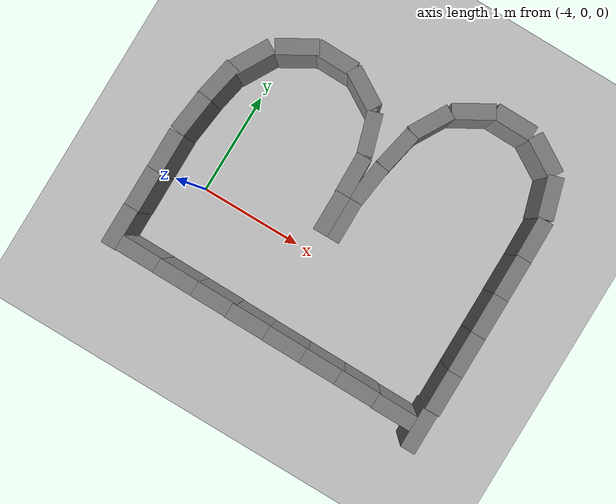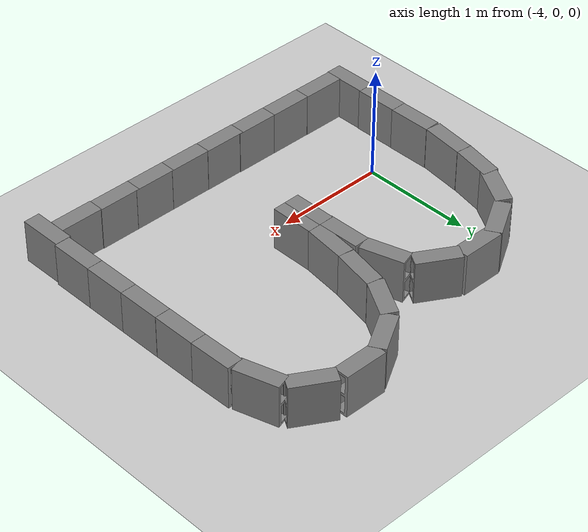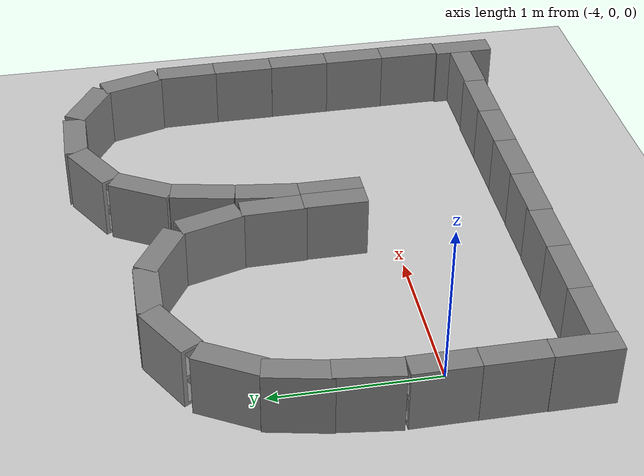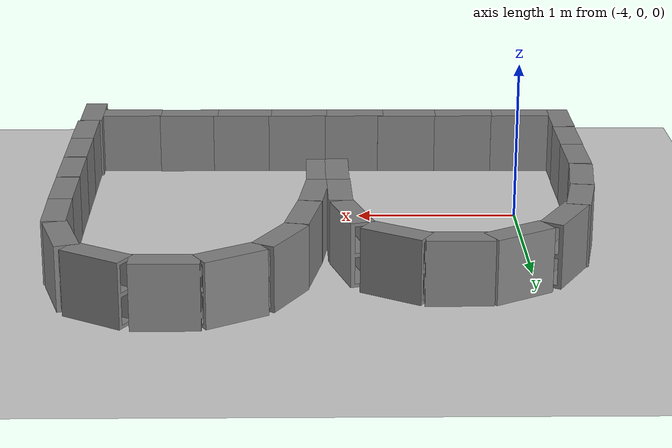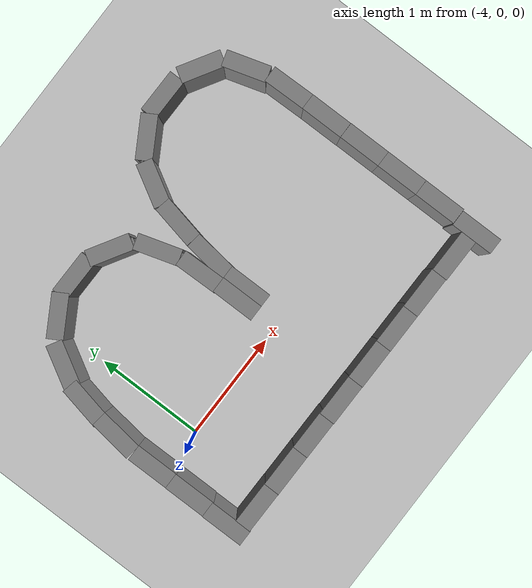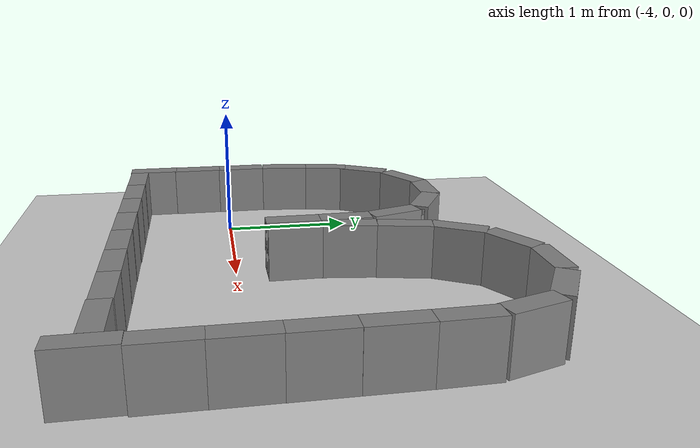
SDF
<sdf version="1.6">
 <world name="default">
  <light name="sun" type="directional">
   <pose>0 0 10 0 -0 0</pose>
   <diffuse>0.8 0.8 0.8 1</diffuse>
   <specular>0.2 0.2 0.2 1</specular>
   <attenuation>
    <range>1000</range>
    <constant>0.9</constant>
    <linear>0.01</linear>
    <quadratic>0.001</quadratic>
   </attenuation>
   <direction>-0.5 0.1 -0.9</direction>
  </light>
  <model name="ground_plane">
   <static>1</static>
   <link name="link">
    <collision name="collision">
     <geometry><plane><normal>0 0 1</normal><size>100 100</size></plane></geometry>
     <surface>
      <contact><collide_bitmask>65535</collide_bitmask></contact>
      <friction><ode><mu>100</mu><mu2>50</mu2></ode></friction>
     </surface>
    </collision>
    <visual name="visual">
     <cast_shadows>0</cast_shadows>
     <geometry><plane><normal>0 0 1</normal><size>100 100</size></plane></geometry>
     <material>
      <script><uri>file://media/materials/scripts/gazebo.material</uri><name>Gazebo/Grey</name></script>
     </material>
    </visual>
   </link>
  </model>
  <physics name="default_physics" default="0" type="ode">
   <real_time_update_rate>1000</real_time_update_rate>
   <max_step_size>0.001</max_step_size>
   <real_time_factor>1</real_time_factor>
   <ode>
    <solver>
     <type>quick</type>
     <iters>150</iters>
     <precon_iters>0</precon_iters>
     <sor>1.4</sor>
     <use_dynamic_moi_rescaling>1</use_dynamic_moi_rescaling>
    </solver>
    <constraints>
     <cfm>1e-05</cfm>
     <erp>0.2</erp>
     <contact_max_correcting_vel>2000</contact_max_correcting_vel>
     <contact_surface_layer>0.01</contact_surface_layer>
    </constraints>
   </ode>
  </physics>
  <scene><ambient>0.4 0.4 0.4 1</ambient><background>0.7 0.7 0.7 1</background><shadows>1</shadows></scene>
  <gravity>0 0 -9.8</gravity>
  <magnetic_field>6e-06 2.3e-05 -4.2e-05</magnetic_field>
  <atmosphere type="adiabatic"/>
  <audio><device>default</device></audio>
  <spherical_coordinates>
   <surface_model>EARTH_WGS84</surface_model>
   <latitude_deg>0</latitude_deg>
   <longitude_deg>0</longitude_deg>
   <elevation>0</elevation>
   <heading_deg>0</heading_deg>
  </spherical_coordinates>
  <model name="cinder_block_wide">
   <link name="link">
    <inertial>
     <pose>0 0 0.071438 0 -0 0</pose>
     <mass>5</mass>
     <inertia>
      <ixx>0.0681466</ixx>
      <ixy>0</ixy>
      <iyy>0.0681466</iyy>
      <ixz>0</ixz>
      <iyz>0</iyz>
      <izz>0.124808</izz>
     </inertia>
    </inertial>
    <visual name="visual">
     <geometry><mesh><uri>model://cinder_block_wide/meshes/cinder_block_wide.dae</uri></mesh></geometry>
    </visual>
    <collision name="top">
     <pose>0 0 0.130175 0 -0 0</pose>
     <geometry><box><size>0.387354 0.387354 0.0254</size></box></geometry>
     <surface>
      <contact><ode><max_vel>0.1</max_vel><min_depth>0.001</min_depth></ode></contact>
      <friction><ode><mu>1</mu><mu2>1</mu2></ode></friction>
     </surface>
    </collision>
    <collision name="bottom">
     <pose>0 0 0.0127 0 -0 0</pose>
     <geometry><box><size>0.387354 0.387354 0.0254</size></box></geometry>
     <surface>
      <contact><ode><max_vel>0.1</max_vel><min_depth>0.001</min_depth></ode></contact>
      <friction><ode><mu>1</mu><mu2>1</mu2></ode></friction>
     </surface>
    </collision>
    <collision name="left">
     <pose>0 -0.183355 0.071438 0 -0 0</pose>
     <geometry><box><size>0.387354 0.020643 0.092075</size></box></geometry>
     <surface>
      <contact><ode><max_vel>0.1</max_vel><min_depth>0.001</min_depth></ode></contact>
      <friction><ode><mu>1</mu><mu2>1</mu2></ode></friction>
     </surface>
    </collision>
    <collision name="right">
     <pose>0 0.183355 0.071438 0 -0 0</pose>
     <geometry><box><size>0.387354 0.020643 0.092075</size></box></geometry>
     <surface>
      <contact><ode><max_vel>0.1</max_vel><min_depth>0.001</min_depth></ode></contact>
      <friction><ode><mu>1</mu><mu2>1</mu2></ode></friction>
     </surface>
    </collision>
    <collision name="middle">
     <pose>0 0 0.071438 0 -0 0</pose>
     <geometry><box><size>0.387354 0.0254 0.092075</size></box></geometry>
     <surface>
      <contact><ode><max_vel>0.1</max_vel><min_depth>0.001</min_depth></ode></contact>
      <friction><ode><mu>1</mu><mu2>1</mu2></ode></friction>
     </surface>
    </collision>
   </link>
   <pose>-1.5034 -0.852041 0.263357 -1.56869 0 -0.003839</pose>
  </model>
  <model name="cinder_block_wide_clone">
   <link name="link">
    <inertial>
     <pose>0 0 0.071438 0 -0 0</pose>
     <mass>5</mass>
     <inertia>
      <ixx>0.0681466</ixx>
      <ixy>0</ixy>
      <iyy>0.0681466</iyy>
      <ixz>0</ixz>
      <iyz>0</iyz>
      <izz>0.124808</izz>
     </inertia>
    </inertial>
    <visual name="visual">
     <geometry><mesh><uri>model://cinder_block_wide/meshes/cinder_block_wide.dae</uri></mesh></geometry>
    </visual>
    <collision name="top">
     <pose>0 0 0.130175 0 -0 0</pose>
     <geometry><box><size>0.387354 0.387354 0.0254</size></box></geometry>
     <surface>
      <contact><ode><max_vel>0.1</max_vel><min_depth>0.001</min_depth></ode></contact>
      <friction><ode><mu>1</mu><mu2>1</mu2></ode></friction>
     </surface>
    </collision>
    <collision name="bottom">
     <pose>0 0 0.0127 0 -0 0</pose>
     <geometry><box><size>0.387354 0.387354 0.0254</size></box></geometry>
     <surface>
      <contact><ode><max_vel>0.1</max_vel><min_depth>0.001</min_depth></ode></contact>
      <friction><ode><mu>1</mu><mu2>1</mu2></ode></friction>
     </surface>
    </collision>
    <collision name="left">
     <pose>0 -0.183355 0.071438 0 -0 0</pose>
     <geometry><box><size>0.387354 0.020643 0.092075</size></box></geometry>
     <surface>
      <contact><ode><max_vel>0.1</max_vel><min_depth>0.001</min_depth></ode></contact>
      <friction><ode><mu>1</mu><mu2>1</mu2></ode></friction>
     </surface>
    </collision>
    <collision name="right">
     <pose>0 0.183355 0.071438 0 -0 0</pose>
     <geometry><box><size>0.387354 0.020643 0.092075</size></box></geometry>
     <surface>
      <contact><ode><max_vel>0.1</max_vel><min_depth>0.001</min_depth></ode></contact>
      <friction><ode><mu>1</mu><mu2>1</mu2></ode></friction>
     </surface>
    </collision>
    <collision name="middle">
     <pose>0 0 0.071438 0 -0 0</pose>
     <geometry><box><size>0.387354 0.0254 0.092075</size></box></geometry>
     <surface>
      <contact><ode><max_vel>0.1</max_vel><min_depth>0.001</min_depth></ode></contact>
      <friction><ode><mu>1</mu><mu2>1</mu2></ode></friction>
     </surface>
    </collision>
   </link>
   <pose>-1.88278 -0.845078 0.263357 -1.56869 0 -0.003839</pose>
  </model>
  <model name="cinder_block_wide_clone_0">
   <link name="link">
    <inertial>
     <pose>0 0 0.071438 0 -0 0</pose>
     <mass>5</mass>
     <inertia>
      <ixx>0.0681466</ixx>
      <ixy>0</ixy>
      <iyy>0.0681466</iyy>
      <ixz>0</ixz>
      <iyz>0</iyz>
      <izz>0.124808</izz>
     </inertia>
    </inertial>
    <visual name="visual">
     <geometry><mesh><uri>model://cinder_block_wide/meshes/cinder_block_wide.dae</uri></mesh></geometry>
    </visual>
    <collision name="top">
     <pose>0 0 0.130175 0 -0 0</pose>
     <geometry><box><size>0.387354 0.387354 0.0254</size></box></geometry>
     <surface>
      <contact><ode><max_vel>0.1</max_vel><min_depth>0.001</min_depth></ode></contact>
      <friction><ode><mu>1</mu><mu2>1</mu2></ode></friction>
     </surface>
    </collision>
    <collision name="bottom">
     <pose>0 0 0.0127 0 -0 0</pose>
     <geometry><box><size>0.387354 0.387354 0.0254</size></box></geometry>
     <surface>
      <contact><ode><max_vel>0.1</max_vel><min_depth>0.001</min_depth></ode></contact>
      <friction><ode><mu>1</mu><mu2>1</mu2></ode></friction>
     </surface>
    </collision>
    <collision name="left">
     <pose>0 -0.183355 0.071438 0 -0 0</pose>
     <geometry><box><size>0.387354 0.020643 0.092075</size></box></geometry>
     <surface>
      <contact><ode><max_vel>0.1</max_vel><min_depth>0.001</min_depth></ode></contact>
      <friction><ode><mu>1</mu><mu2>1</mu2></ode></friction>
     </surface>
    </collision>
    <collision name="right">
     <pose>0 0.183355 0.071438 0 -0 0</pose>
     <geometry><box><size>0.387354 0.020643 0.092075</size></box></geometry>
     <surface>
      <contact><ode><max_vel>0.1</max_vel><min_depth>0.001</min_depth></ode></contact>
      <friction><ode><mu>1</mu><mu2>1</mu2></ode></friction>
     </surface>
    </collision>
    <collision name="middle">
     <pose>0 0 0.071438 0 -0 0</pose>
     <geometry><box><size>0.387354 0.0254 0.092075</size></box></geometry>
     <surface>
      <contact><ode><max_vel>0.1</max_vel><min_depth>0.001</min_depth></ode></contact>
      <friction><ode><mu>1</mu><mu2>1</mu2></ode></friction>
     </surface>
    </collision>
   </link>
   <pose>-2.24071 -0.843014 0.263357 -1.56869 0 -0.003839</pose>
  </model>
  <model name="cinder_block_wide_clone_1">
   <link name="link">
    <inertial>
     <pose>0 0 0.071438 0 -0 0</pose>
     <mass>5</mass>
     <inertia>
      <ixx>0.0681466</ixx>
      <ixy>0</ixy>
      <iyy>0.0681466</iyy>
      <ixz>0</ixz>
      <iyz>0</iyz>
      <izz>0.124808</izz>
     </inertia>
    </inertial>
    <visual name="visual">
     <geometry><mesh><uri>model://cinder_block_wide/meshes/cinder_block_wide.dae</uri></mesh></geometry>
    </visual>
    <collision name="top">
     <pose>0 0 0.130175 0 -0 0</pose>
     <geometry><box><size>0.387354 0.387354 0.0254</size></box></geometry>
     <surface>
      <contact><ode><max_vel>0.1</max_vel><min_depth>0.001</min_depth></ode></contact>
      <friction><ode><mu>1</mu><mu2>1</mu2></ode></friction>
     </surface>
    </collision>
    <collision name="bottom">
     <pose>0 0 0.0127 0 -0 0</pose>
     <geometry><box><size>0.387354 0.387354 0.0254</size></box></geometry>
     <surface>
      <contact><ode><max_vel>0.1</max_vel><min_depth>0.001</min_depth></ode></contact>
      <friction><ode><mu>1</mu><mu2>1</mu2></ode></friction>
     </surface>
    </collision>
    <collision name="left">
     <pose>0 -0.183355 0.071438 0 -0 0</pose>
     <geometry><box><size>0.387354 0.020643 0.092075</size></box></geometry>
     <surface>
      <contact><ode><max_vel>0.1</max_vel><min_depth>0.001</min_depth></ode></contact>
      <friction><ode><mu>1</mu><mu2>1</mu2></ode></friction>
     </surface>
    </collision>
    <collision name="right">
     <pose>0 0.183355 0.071438 0 -0 0</pose>
     <geometry><box><size>0.387354 0.020643 0.092075</size></box></geometry>
     <surface>
      <contact><ode><max_vel>0.1</max_vel><min_depth>0.001</min_depth></ode></contact>
      <friction><ode><mu>1</mu><mu2>1</mu2></ode></friction>
     </surface>
    </collision>
    <collision name="middle">
     <pose>0 0 0.071438 0 -0 0</pose>
     <geometry><box><size>0.387354 0.0254 0.092075</size></box></geometry>
     <surface>
      <contact><ode><max_vel>0.1</max_vel><min_depth>0.001</min_depth></ode></contact>
      <friction><ode><mu>1</mu><mu2>1</mu2></ode></friction>
     </surface>
    </collision>
   </link>
   <pose>-2.61163 -0.840837 0.263357 -1.56869 0 -0.003839</pose>
  </model>
  <model name="cinder_block_wide_clone_2">
   <link name="link">
    <inertial>
     <pose>0 0 0.071438 0 -0 0</pose>
     <mass>5</mass>
     <inertia>
      <ixx>0.0681466</ixx>
      <ixy>0</ixy>
      <iyy>0.0681466</iyy>
      <ixz>0</ixz>
      <iyz>0</iyz>
      <izz>0.124808</izz>
     </inertia>
    </inertial>
    <visual name="visual">
     <geometry><mesh><uri>model://cinder_block_wide/meshes/cinder_block_wide.dae</uri></mesh></geometry>
    </visual>
    <collision name="top">
     <pose>0 0 0.130175 0 -0 0</pose>
     <geometry><box><size>0.387354 0.387354 0.0254</size></box></geometry>
     <surface>
      <contact><ode><max_vel>0.1</max_vel><min_depth>0.001</min_depth></ode></contact>
      <friction><ode><mu>1</mu><mu2>1</mu2></ode></friction>
     </surface>
    </collision>
    <collision name="bottom">
     <pose>0 0 0.0127 0 -0 0</pose>
     <geometry><box><size>0.387354 0.387354 0.0254</size></box></geometry>
     <surface>
      <contact><ode><max_vel>0.1</max_vel><min_depth>0.001</min_depth></ode></contact>
      <friction><ode><mu>1</mu><mu2>1</mu2></ode></friction>
     </surface>
    </collision>
    <collision name="left">
     <pose>0 -0.183355 0.071438 0 -0 0</pose>
     <geometry><box><size>0.387354 0.020643 0.092075</size></box></geometry>
     <surface>
      <contact><ode><max_vel>0.1</max_vel><min_depth>0.001</min_depth></ode></contact>
      <friction><ode><mu>1</mu><mu2>1</mu2></ode></friction>
     </surface>
    </collision>
    <collision name="right">
     <pose>0 0.183355 0.071438 0 -0 0</pose>
     <geometry><box><size>0.387354 0.020643 0.092075</size></box></geometry>
     <surface>
      <contact><ode><max_vel>0.1</max_vel><min_depth>0.001</min_depth></ode></contact>
      <friction><ode><mu>1</mu><mu2>1</mu2></ode></friction>
     </surface>
    </collision>
    <collision name="middle">
     <pose>0 0 0.071438 0 -0 0</pose>
     <geometry><box><size>0.387354 0.0254 0.092075</size></box></geometry>
     <surface>
      <contact><ode><max_vel>0.1</max_vel><min_depth>0.001</min_depth></ode></contact>
      <friction><ode><mu>1</mu><mu2>1</mu2></ode></friction>
     </surface>
    </collision>
   </link>
   <pose>-2.99041 -0.837587 0.263357 -1.56869 0 -0.003839</pose>
  </model>
  <model name="cinder_block_wide_clone_3">
   <link name="link">
    <inertial>
     <pose>0 0 0.071438 0 -0 0</pose>
     <mass>5</mass>
     <inertia>
      <ixx>0.0681466</ixx>
      <ixy>0</ixy>
      <iyy>0.0681466</iyy>
      <ixz>0</ixz>
      <iyz>0</iyz>
      <izz>0.124808</izz>
     </inertia>
    </inertial>
    <visual name="visual">
     <geometry><mesh><uri>model://cinder_block_wide/meshes/cinder_block_wide.dae</uri></mesh></geometry>
    </visual>
    <collision name="top">
     <pose>0 0 0.130175 0 -0 0</pose>
     <geometry><box><size>0.387354 0.387354 0.0254</size></box></geometry>
     <surface>
      <contact><ode><max_vel>0.1</max_vel><min_depth>0.001</min_depth></ode></contact>
      <friction><ode><mu>1</mu><mu2>1</mu2></ode></friction>
     </surface>
    </collision>
    <collision name="bottom">
     <pose>0 0 0.0127 0 -0 0</pose>
     <geometry><box><size>0.387354 0.387354 0.0254</size></box></geometry>
     <surface>
      <contact><ode><max_vel>0.1</max_vel><min_depth>0.001</min_depth></ode></contact>
      <friction><ode><mu>1</mu><mu2>1</mu2></ode></friction>
     </surface>
    </collision>
    <collision name="left">
     <pose>0 -0.183355 0.071438 0 -0 0</pose>
     <geometry><box><size>0.387354 0.020643 0.092075</size></box></geometry>
     <surface>
      <contact><ode><max_vel>0.1</max_vel><min_depth>0.001</min_depth></ode></contact>
      <friction><ode><mu>1</mu><mu2>1</mu2></ode></friction>
     </surface>
    </collision>
    <collision name="right">
     <pose>0 0.183355 0.071438 0 -0 0</pose>
     <geometry><box><size>0.387354 0.020643 0.092075</size></box></geometry>
     <surface>
      <contact><ode><max_vel>0.1</max_vel><min_depth>0.001</min_depth></ode></contact>
      <friction><ode><mu>1</mu><mu2>1</mu2></ode></friction>
     </surface>
    </collision>
    <collision name="middle">
     <pose>0 0 0.071438 0 -0 0</pose>
     <geometry><box><size>0.387354 0.0254 0.092075</size></box></geometry>
     <surface>
      <contact><ode><max_vel>0.1</max_vel><min_depth>0.001</min_depth></ode></contact>
      <friction><ode><mu>1</mu><mu2>1</mu2></ode></friction>
     </surface>
    </collision>
   </link>
   <pose>-3.34042 -0.832439 0.263357 -1.56869 0 -0.003839</pose>
  </model>
  <model name="cinder_block_wide_clone_4">
   <link name="link">
    <inertial>
     <pose>0 0 0.071438 0 -0 0</pose>
     <mass>5</mass>
     <inertia>
      <ixx>0.0681466</ixx>
      <ixy>0</ixy>
      <iyy>0.0681466</iyy>
      <ixz>0</ixz>
      <iyz>0</iyz>
      <izz>0.124808</izz>
     </inertia>
    </inertial>
    <visual name="visual">
     <geometry><mesh><uri>model://cinder_block_wide/meshes/cinder_block_wide.dae</uri></mesh></geometry>
    </visual>
    <collision name="top">
     <pose>0 0 0.130175 0 -0 0</pose>
     <geometry><box><size>0.387354 0.387354 0.0254</size></box></geometry>
     <surface>
      <contact><ode><max_vel>0.1</max_vel><min_depth>0.001</min_depth></ode></contact>
      <friction><ode><mu>1</mu><mu2>1</mu2></ode></friction>
     </surface>
    </collision>
    <collision name="bottom">
     <pose>0 0 0.0127 0 -0 0</pose>
     <geometry><box><size>0.387354 0.387354 0.0254</size></box></geometry>
     <surface>
      <contact><ode><max_vel>0.1</max_vel><min_depth>0.001</min_depth></ode></contact>
      <friction><ode><mu>1</mu><mu2>1</mu2></ode></friction>
     </surface>
    </collision>
    <collision name="left">
     <pose>0 -0.183355 0.071438 0 -0 0</pose>
     <geometry><box><size>0.387354 0.020643 0.092075</size></box></geometry>
     <surface>
      <contact><ode><max_vel>0.1</max_vel><min_depth>0.001</min_depth></ode></contact>
      <friction><ode><mu>1</mu><mu2>1</mu2></ode></friction>
     </surface>
    </collision>
    <collision name="right">
     <pose>0 0.183355 0.071438 0 -0 0</pose>
     <geometry><box><size>0.387354 0.020643 0.092075</size></box></geometry>
     <surface>
      <contact><ode><max_vel>0.1</max_vel><min_depth>0.001</min_depth></ode></contact>
      <friction><ode><mu>1</mu><mu2>1</mu2></ode></friction>
     </surface>
    </collision>
    <collision name="middle">
     <pose>0 0 0.071438 0 -0 0</pose>
     <geometry><box><size>0.387354 0.0254 0.092075</size></box></geometry>
     <surface>
      <contact><ode><max_vel>0.1</max_vel><min_depth>0.001</min_depth></ode></contact>
      <friction><ode><mu>1</mu><mu2>1</mu2></ode></friction>
     </surface>
    </collision>
   </link>
   <pose>-3.72096 -0.830221 0.263357 -1.56869 0 -0.003839</pose>
  </model>
  <model name="cinder_block_wide_clone_5">
   <link name="link">
    <inertial>
     <pose>0 0 0.071438 0 -0 0</pose>
     <mass>5</mass>
     <inertia>
      <ixx>0.0681466</ixx>
      <ixy>0</ixy>
      <iyy>0.0681466</iyy>
      <ixz>0</ixz>
      <iyz>0</iyz>
      <izz>0.124808</izz>
     </inertia>
    </inertial>
    <visual name="visual">
     <geometry><mesh><uri>model://cinder_block_wide/meshes/cinder_block_wide.dae</uri></mesh></geometry>
    </visual>
    <collision name="top">
     <pose>0 0 0.130175 0 -0 0</pose>
     <geometry><box><size>0.387354 0.387354 0.0254</size></box></geometry>
     <surface>
      <contact><ode><max_vel>0.1</max_vel><min_depth>0.001</min_depth></ode></contact>
      <friction><ode><mu>1</mu><mu2>1</mu2></ode></friction>
     </surface>
    </collision>
    <collision name="bottom">
     <pose>0 0 0.0127 0 -0 0</pose>
     <geometry><box><size>0.387354 0.387354 0.0254</size></box></geometry>
     <surface>
      <contact><ode><max_vel>0.1</max_vel><min_depth>0.001</min_depth></ode></contact>
      <friction><ode><mu>1</mu><mu2>1</mu2></ode></friction>
     </surface>
    </collision>
    <collision name="left">
     <pose>0 -0.183355 0.071438 0 -0 0</pose>
     <geometry><box><size>0.387354 0.020643 0.092075</size></box></geometry>
     <surface>
      <contact><ode><max_vel>0.1</max_vel><min_depth>0.001</min_depth></ode></contact>
      <friction><ode><mu>1</mu><mu2>1</mu2></ode></friction>
     </surface>
    </collision>
    <collision name="right">
     <pose>0 0.183355 0.071438 0 -0 0</pose>
     <geometry><box><size>0.387354 0.020643 0.092075</size></box></geometry>
     <surface>
      <contact><ode><max_vel>0.1</max_vel><min_depth>0.001</min_depth></ode></contact>
      <friction><ode><mu>1</mu><mu2>1</mu2></ode></friction>
     </surface>
    </collision>
    <collision name="middle">
     <pose>0 0 0.071438 0 -0 0</pose>
     <geometry><box><size>0.387354 0.0254 0.092075</size></box></geometry>
     <surface>
      <contact><ode><max_vel>0.1</max_vel><min_depth>0.001</min_depth></ode></contact>
      <friction><ode><mu>1</mu><mu2>1</mu2></ode></friction>
     </surface>
    </collision>
   </link>
   <pose>-4.10015 -0.827299 0.263357 -1.56869 0 -0.003839</pose>
  </model>
  <model name="cinder_block_wide_clone_6">
   <link name="link">
    <inertial>
     <pose>0 0 0.071438 0 -0 0</pose>
     <mass>5</mass>
     <inertia>
      <ixx>0.0681466</ixx>
      <ixy>0</ixy>
      <iyy>0.0681466</iyy>
      <ixz>0</ixz>
      <iyz>0</iyz>
      <izz>0.124808</izz>
     </inertia>
    </inertial>
    <visual name="visual">
     <geometry><mesh><uri>model://cinder_block_wide/meshes/cinder_block_wide.dae</uri></mesh></geometry>
    </visual>
    <collision name="top">
     <pose>0 0 0.130175 0 -0 0</pose>
     <geometry><box><size>0.387354 0.387354 0.0254</size></box></geometry>
     <surface>
      <contact><ode><max_vel>0.1</max_vel><min_depth>0.001</min_depth></ode></contact>
      <friction><ode><mu>1</mu><mu2>1</mu2></ode></friction>
     </surface>
    </collision>
    <collision name="bottom">
     <pose>0 0 0.0127 0 -0 0</pose>
     <geometry><box><size>0.387354 0.387354 0.0254</size></box></geometry>
     <surface>
      <contact><ode><max_vel>0.1</max_vel><min_depth>0.001</min_depth></ode></contact>
      <friction><ode><mu>1</mu><mu2>1</mu2></ode></friction>
     </surface>
    </collision>
    <collision name="left">
     <pose>0 -0.183355 0.071438 0 -0 0</pose>
     <geometry><box><size>0.387354 0.020643 0.092075</size></box></geometry>
     <surface>
      <contact><ode><max_vel>0.1</max_vel><min_depth>0.001</min_depth></ode></contact>
      <friction><ode><mu>1</mu><mu2>1</mu2></ode></friction>
     </surface>
    </collision>
    <collision name="right">
     <pose>0 0.183355 0.071438 0 -0 0</pose>
     <geometry><box><size>0.387354 0.020643 0.092075</size></box></geometry>
     <surface>
      <contact><ode><max_vel>0.1</max_vel><min_depth>0.001</min_depth></ode></contact>
      <friction><ode><mu>1</mu><mu2>1</mu2></ode></friction>
     </surface>
    </collision>
    <collision name="middle">
     <pose>0 0 0.071438 0 -0 0</pose>
     <geometry><box><size>0.387354 0.0254 0.092075</size></box></geometry>
     <surface>
      <contact><ode><max_vel>0.1</max_vel><min_depth>0.001</min_depth></ode></contact>
      <friction><ode><mu>1</mu><mu2>1</mu2></ode></friction>
     </surface>
    </collision>
   </link>
   <pose>-4.43202 -0.638749 0.263357 -1.57078 0.002106 -1.56659</pose>
  </model>
  <model name="cinder_block_wide_clone_6_clone">
   <link name="link">
    <inertial>
     <pose>0 0 0.071438 0 -0 0</pose>
     <mass>5</mass>
     <inertia>
      <ixx>0.0681466</ixx>
      <ixy>0</ixy>
      <iyy>0.0681466</iyy>
      <ixz>0</ixz>
      <iyz>0</iyz>
      <izz>0.124808</izz>
     </inertia>
    </inertial>
    <visual name="visual">
     <geometry><mesh><uri>model://cinder_block_wide/meshes/cinder_block_wide.dae</uri></mesh></geometry>
    </visual>
    <collision name="top">
     <pose>0 0 0.130175 0 -0 0</pose>
     <geometry><box><size>0.387354 0.387354 0.0254</size></box></geometry>
     <surface>
      <contact><ode><max_vel>0.1</max_vel><min_depth>0.001</min_depth></ode></contact>
      <friction><ode><mu>1</mu><mu2>1</mu2></ode></friction>
     </surface>
    </collision>
    <collision name="bottom">
     <pose>0 0 0.0127 0 -0 0</pose>
     <geometry><box><size>0.387354 0.387354 0.0254</size></box></geometry>
     <surface>
      <contact><ode><max_vel>0.1</max_vel><min_depth>0.001</min_depth></ode></contact>
      <friction><ode><mu>1</mu><mu2>1</mu2></ode></friction>
     </surface>
    </collision>
    <collision name="left">
     <pose>0 -0.183355 0.071438 0 -0 0</pose>
     <geometry><box><size>0.387354 0.020643 0.092075</size></box></geometry>
     <surface>
      <contact><ode><max_vel>0.1</max_vel><min_depth>0.001</min_depth></ode></contact>
      <friction><ode><mu>1</mu><mu2>1</mu2></ode></friction>
     </surface>
    </collision>
    <collision name="right">
     <pose>0 0.183355 0.071438 0 -0 0</pose>
     <geometry><box><size>0.387354 0.020643 0.092075</size></box></geometry>
     <surface>
      <contact><ode><max_vel>0.1</max_vel><min_depth>0.001</min_depth></ode></contact>
      <friction><ode><mu>1</mu><mu2>1</mu2></ode></friction>
     </surface>
    </collision>
    <collision name="middle">
     <pose>0 0 0.071438 0 -0 0</pose>
     <geometry><box><size>0.387354 0.0254 0.092075</size></box></geometry>
     <surface>
      <contact><ode><max_vel>0.1</max_vel><min_depth>0.001</min_depth></ode></contact>
      <friction><ode><mu>1</mu><mu2>1</mu2></ode></friction>
     </surface>
    </collision>
   </link>
   <pose>-4.43004 -0.260362 0.263357 -1.57078 0.002106 -1.56659</pose>
  </model>
  <model name="cinder_block_wide_clone_6_clone_0">
   <link name="link">
    <inertial>
     <pose>0 0 0.071438 0 -0 0</pose>
     <mass>5</mass>
     <inertia>
      <ixx>0.0681466</ixx>
      <ixy>0</ixy>
      <iyy>0.0681466</iyy>
      <ixz>0</ixz>
      <iyz>0</iyz>
      <izz>0.124808</izz>
     </inertia>
    </inertial>
    <visual name="visual">
     <geometry><mesh><uri>model://cinder_block_wide/meshes/cinder_block_wide.dae</uri></mesh></geometry>
    </visual>
    <collision name="top">
     <pose>0 0 0.130175 0 -0 0</pose>
     <geometry><box><size>0.387354 0.387354 0.0254</size></box></geometry>
     <surface>
      <contact><ode><max_vel>0.1</max_vel><min_depth>0.001</min_depth></ode></contact>
      <friction><ode><mu>1</mu><mu2>1</mu2></ode></friction>
     </surface>
    </collision>
    <collision name="bottom">
     <pose>0 0 0.0127 0 -0 0</pose>
     <geometry><box><size>0.387354 0.387354 0.0254</size></box></geometry>
     <surface>
      <contact><ode><max_vel>0.1</max_vel><min_depth>0.001</min_depth></ode></contact>
      <friction><ode><mu>1</mu><mu2>1</mu2></ode></friction>
     </surface>
    </collision>
    <collision name="left">
     <pose>0 -0.183355 0.071438 0 -0 0</pose>
     <geometry><box><size>0.387354 0.020643 0.092075</size></box></geometry>
     <surface>
      <contact><ode><max_vel>0.1</max_vel><min_depth>0.001</min_depth></ode></contact>
      <friction><ode><mu>1</mu><mu2>1</mu2></ode></friction>
     </surface>
    </collision>
    <collision name="right">
     <pose>0 0.183355 0.071438 0 -0 0</pose>
     <geometry><box><size>0.387354 0.020643 0.092075</size></box></geometry>
     <surface>
      <contact><ode><max_vel>0.1</max_vel><min_depth>0.001</min_depth></ode></contact>
      <friction><ode><mu>1</mu><mu2>1</mu2></ode></friction>
     </surface>
    </collision>
    <collision name="middle">
     <pose>0 0 0.071438 0 -0 0</pose>
     <geometry><box><size>0.387354 0.0254 0.092075</size></box></geometry>
     <surface>
      <contact><ode><max_vel>0.1</max_vel><min_depth>0.001</min_depth></ode></contact>
      <friction><ode><mu>1</mu><mu2>1</mu2></ode></friction>
     </surface>
    </collision>
   </link>
   <pose>-4.43002 0.120318 0.263357 -1.57078 0.002106 -1.56659</pose>
  </model>
  <model name="cinder_block_wide_clone_6_clone_1">
   <link name="link">
    <inertial>
     <pose>0 0 0.071438 0 -0 0</pose>
     <mass>5</mass>
     <inertia>
      <ixx>0.0681466</ixx>
      <ixy>0</ixy>
      <iyy>0.0681466</iyy>
      <ixz>0</ixz>
      <iyz>0</iyz>
      <izz>0.124808</izz>
     </inertia>
    </inertial>
    <visual name="visual">
     <geometry><mesh><uri>model://cinder_block_wide/meshes/cinder_block_wide.dae</uri></mesh></geometry>
    </visual>
    <collision name="top">
     <pose>0 0 0.130175 0 -0 0</pose>
     <geometry><box><size>0.387354 0.387354 0.0254</size></box></geometry>
     <surface>
      <contact><ode><max_vel>0.1</max_vel><min_depth>0.001</min_depth></ode></contact>
      <friction><ode><mu>1</mu><mu2>1</mu2></ode></friction>
     </surface>
    </collision>
    <collision name="bottom">
     <pose>0 0 0.0127 0 -0 0</pose>
     <geometry><box><size>0.387354 0.387354 0.0254</size></box></geometry>
     <surface>
      <contact><ode><max_vel>0.1</max_vel><min_depth>0.001</min_depth></ode></contact>
      <friction><ode><mu>1</mu><mu2>1</mu2></ode></friction>
     </surface>
    </collision>
    <collision name="left">
     <pose>0 -0.183355 0.071438 0 -0 0</pose>
     <geometry><box><size>0.387354 0.020643 0.092075</size></box></geometry>
     <surface>
      <contact><ode><max_vel>0.1</max_vel><min_depth>0.001</min_depth></ode></contact>
      <friction><ode><mu>1</mu><mu2>1</mu2></ode></friction>
     </surface>
    </collision>
    <collision name="right">
     <pose>0 0.183355 0.071438 0 -0 0</pose>
     <geometry><box><size>0.387354 0.020643 0.092075</size></box></geometry>
     <surface>
      <contact><ode><max_vel>0.1</max_vel><min_depth>0.001</min_depth></ode></contact>
      <friction><ode><mu>1</mu><mu2>1</mu2></ode></friction>
     </surface>
    </collision>
    <collision name="middle">
     <pose>0 0 0.071438 0 -0 0</pose>
     <geometry><box><size>0.387354 0.0254 0.092075</size></box></geometry>
     <surface>
      <contact><ode><max_vel>0.1</max_vel><min_depth>0.001</min_depth></ode></contact>
      <friction><ode><mu>1</mu><mu2>1</mu2></ode></friction>
     </surface>
    </collision>
   </link>
   <pose>-4.40892 0.523018 0.263357 -1.57105 0.00209 -1.6971</pose>
  </model>
  <model name="cinder_block_wide_clone_6_clone_2">
   <link name="link">
    <inertial>
     <pose>0 0 0.071438 0 -0 0</pose>
     <mass>5</mass>
     <inertia>
      <ixx>0.0681466</ixx>
      <ixy>0</ixy>
      <iyy>0.0681466</iyy>
      <ixz>0</ixz>
      <iyz>0</iyz>
      <izz>0.124808</izz>
     </inertia>
    </inertial>
    <visual name="visual">
     <geometry><mesh><uri>model://cinder_block_wide/meshes/cinder_block_wide.dae</uri></mesh></geometry>
    </visual>
    <collision name="top">
     <pose>0 0 0.130175 0 -0 0</pose>
     <geometry><box><size>0.387354 0.387354 0.0254</size></box></geometry>
     <surface>
      <contact><ode><max_vel>0.1</max_vel><min_depth>0.001</min_depth></ode></contact>
      <friction><ode><mu>1</mu><mu2>1</mu2></ode></friction>
     </surface>
    </collision>
    <collision name="bottom">
     <pose>0 0 0.0127 0 -0 0</pose>
     <geometry><box><size>0.387354 0.387354 0.0254</size></box></geometry>
     <surface>
      <contact><ode><max_vel>0.1</max_vel><min_depth>0.001</min_depth></ode></contact>
      <friction><ode><mu>1</mu><mu2>1</mu2></ode></friction>
     </surface>
    </collision>
    <collision name="left">
     <pose>0 -0.183355 0.071438 0 -0 0</pose>
     <geometry><box><size>0.387354 0.020643 0.092075</size></box></geometry>
     <surface>
      <contact><ode><max_vel>0.1</max_vel><min_depth>0.001</min_depth></ode></contact>
      <friction><ode><mu>1</mu><mu2>1</mu2></ode></friction>
     </surface>
    </collision>
    <collision name="right">
     <pose>0 0.183355 0.071438 0 -0 0</pose>
     <geometry><box><size>0.387354 0.020643 0.092075</size></box></geometry>
     <surface>
      <contact><ode><max_vel>0.1</max_vel><min_depth>0.001</min_depth></ode></contact>
      <friction><ode><mu>1</mu><mu2>1</mu2></ode></friction>
     </surface>
    </collision>
    <collision name="middle">
     <pose>0 0 0.071438 0 -0 0</pose>
     <geometry><box><size>0.387354 0.0254 0.092075</size></box></geometry>
     <surface>
      <contact><ode><max_vel>0.1</max_vel><min_depth>0.001</min_depth></ode></contact>
      <friction><ode><mu>1</mu><mu2>1</mu2></ode></friction>
     </surface>
    </collision>
   </link>
   <pose>-2.927 0.406046 0.263357 -1.57078 0.002106 -1.56659</pose>
  </model>
  <model name="cinder_block_wide_clone_6_clone_1_clone">
   <link name="link">
    <inertial>
     <pose>0 0 0.071438 0 -0 0</pose>
     <mass>5</mass>
     <inertia>
      <ixx>0.0681466</ixx>
      <ixy>0</ixy>
      <iyy>0.0681466</iyy>
      <ixz>0</ixz>
      <iyz>0</iyz>
      <izz>0.124808</izz>
     </inertia>
    </inertial>
    <visual name="visual">
     <geometry><mesh><uri>model://cinder_block_wide/meshes/cinder_block_wide.dae</uri></mesh></geometry>
    </visual>
    <collision name="top">
     <pose>0 0 0.130175 0 -0 0</pose>
     <geometry><box><size>0.387354 0.387354 0.0254</size></box></geometry>
     <surface>
      <contact><ode><max_vel>0.1</max_vel><min_depth>0.001</min_depth></ode></contact>
      <friction><ode><mu>1</mu><mu2>1</mu2></ode></friction>
     </surface>
    </collision>
    <collision name="bottom">
     <pose>0 0 0.0127 0 -0 0</pose>
     <geometry><box><size>0.387354 0.387354 0.0254</size></box></geometry>
     <surface>
      <contact><ode><max_vel>0.1</max_vel><min_depth>0.001</min_depth></ode></contact>
      <friction><ode><mu>1</mu><mu2>1</mu2></ode></friction>
     </surface>
    </collision>
    <collision name="left">
     <pose>0 -0.183355 0.071438 0 -0 0</pose>
     <geometry><box><size>0.387354 0.020643 0.092075</size></box></geometry>
     <surface>
      <contact><ode><max_vel>0.1</max_vel><min_depth>0.001</min_depth></ode></contact>
      <friction><ode><mu>1</mu><mu2>1</mu2></ode></friction>
     </surface>
    </collision>
    <collision name="right">
     <pose>0 0.183355 0.071438 0 -0 0</pose>
     <geometry><box><size>0.387354 0.020643 0.092075</size></box></geometry>
     <surface>
      <contact><ode><max_vel>0.1</max_vel><min_depth>0.001</min_depth></ode></contact>
      <friction><ode><mu>1</mu><mu2>1</mu2></ode></friction>
     </surface>
    </collision>
    <collision name="middle">
     <pose>0 0 0.071438 0 -0 0</pose>
     <geometry><box><size>0.387354 0.0254 0.092075</size></box></geometry>
     <surface>
      <contact><ode><max_vel>0.1</max_vel><min_depth>0.001</min_depth></ode></contact>
      <friction><ode><mu>1</mu><mu2>1</mu2></ode></friction>
     </surface>
    </collision>
   </link>
   <pose>-4.3535 0.883133 0.263357 -1.5712 0.002065 -1.77123</pose>
  </model>
  <model name="cinder_block_wide_clone_6_clone_1_clone_0">
   <link name="link">
    <inertial>
     <pose>0 0 0.071438 0 -0 0</pose>
     <mass>5</mass>
     <inertia>
      <ixx>0.0681466</ixx>
      <ixy>0</ixy>
      <iyy>0.0681466</iyy>
      <ixz>0</ixz>
      <iyz>0</iyz>
      <izz>0.124808</izz>
     </inertia>
    </inertial>
    <visual name="visual">
     <geometry><mesh><uri>model://cinder_block_wide/meshes/cinder_block_wide.dae</uri></mesh></geometry>
    </visual>
    <collision name="top">
     <pose>0 0 0.130175 0 -0 0</pose>
     <geometry><box><size>0.387354 0.387354 0.0254</size></box></geometry>
     <surface>
      <contact><ode><max_vel>0.1</max_vel><min_depth>0.001</min_depth></ode></contact>
      <friction><ode><mu>1</mu><mu2>1</mu2></ode></friction>
     </surface>
    </collision>
    <collision name="bottom">
     <pose>0 0 0.0127 0 -0 0</pose>
     <geometry><box><size>0.387354 0.387354 0.0254</size></box></geometry>
     <surface>
      <contact><ode><max_vel>0.1</max_vel><min_depth>0.001</min_depth></ode></contact>
      <friction><ode><mu>1</mu><mu2>1</mu2></ode></friction>
     </surface>
    </collision>
    <collision name="left">
     <pose>0 -0.183355 0.071438 0 -0 0</pose>
     <geometry><box><size>0.387354 0.020643 0.092075</size></box></geometry>
     <surface>
      <contact><ode><max_vel>0.1</max_vel><min_depth>0.001</min_depth></ode></contact>
      <friction><ode><mu>1</mu><mu2>1</mu2></ode></friction>
     </surface>
    </collision>
    <collision name="right">
     <pose>0 0.183355 0.071438 0 -0 0</pose>
     <geometry><box><size>0.387354 0.020643 0.092075</size></box></geometry>
     <surface>
      <contact><ode><max_vel>0.1</max_vel><min_depth>0.001</min_depth></ode></contact>
      <friction><ode><mu>1</mu><mu2>1</mu2></ode></friction>
     </surface>
    </collision>
    <collision name="middle">
     <pose>0 0 0.071438 0 -0 0</pose>
     <geometry><box><size>0.387354 0.0254 0.092075</size></box></geometry>
     <surface>
      <contact><ode><max_vel>0.1</max_vel><min_depth>0.001</min_depth></ode></contact>
      <friction><ode><mu>1</mu><mu2>1</mu2></ode></friction>
     </surface>
    </collision>
   </link>
   <pose>-4.20601 1.23973 0.263357 -1.57183 0.001834 -2.08968</pose>
  </model>
  <model name="cinder_block_wide_clone_6_clone_1_clone_1">
   <link name="link">
    <inertial>
     <pose>0 0 0.071438 0 -0 0</pose>
     <mass>5</mass>
     <inertia>
      <ixx>0.0681466</ixx>
      <ixy>0</ixy>
      <iyy>0.0681466</iyy>
      <ixz>0</ixz>
      <iyz>0</iyz>
      <izz>0.124808</izz>
     </inertia>
    </inertial>
    <visual name="visual">
     <geometry><mesh><uri>model://cinder_block_wide/meshes/cinder_block_wide.dae</uri></mesh></geometry>
    </visual>
    <collision name="top">
     <pose>0 0 0.130175 0 -0 0</pose>
     <geometry><box><size>0.387354 0.387354 0.0254</size></box></geometry>
     <surface>
      <contact><ode><max_vel>0.1</max_vel><min_depth>0.001</min_depth></ode></contact>
      <friction><ode><mu>1</mu><mu2>1</mu2></ode></friction>
     </surface>
    </collision>
    <collision name="bottom">
     <pose>0 0 0.0127 0 -0 0</pose>
     <geometry><box><size>0.387354 0.387354 0.0254</size></box></geometry>
     <surface>
      <contact><ode><max_vel>0.1</max_vel><min_depth>0.001</min_depth></ode></contact>
      <friction><ode><mu>1</mu><mu2>1</mu2></ode></friction>
     </surface>
    </collision>
    <collision name="left">
     <pose>0 -0.183355 0.071438 0 -0 0</pose>
     <geometry><box><size>0.387354 0.020643 0.092075</size></box></geometry>
     <surface>
      <contact><ode><max_vel>0.1</max_vel><min_depth>0.001</min_depth></ode></contact>
      <friction><ode><mu>1</mu><mu2>1</mu2></ode></friction>
     </surface>
    </collision>
    <collision name="right">
     <pose>0 0.183355 0.071438 0 -0 0</pose>
     <geometry><box><size>0.387354 0.020643 0.092075</size></box></geometry>
     <surface>
      <contact><ode><max_vel>0.1</max_vel><min_depth>0.001</min_depth></ode></contact>
      <friction><ode><mu>1</mu><mu2>1</mu2></ode></friction>
     </surface>
    </collision>
    <collision name="middle">
     <pose>0 0 0.071438 0 -0 0</pose>
     <geometry><box><size>0.387354 0.0254 0.092075</size></box></geometry>
     <surface>
      <contact><ode><max_vel>0.1</max_vel><min_depth>0.001</min_depth></ode></contact>
      <friction><ode><mu>1</mu><mu2>1</mu2></ode></friction>
     </surface>
    </collision>
   </link>
   <pose>-3.89223 1.5428 0.263357 -1.57261 0.001075 -2.61103</pose>
  </model>
  <model name="cinder_block_wide_clone_6_clone_1_clone_1_clone">
   <link name="link">
    <inertial>
     <pose>0 0 0.071438 0 -0 0</pose>
     <mass>5</mass>
     <inertia>
      <ixx>0.0681466</ixx>
      <ixy>0</ixy>
      <iyy>0.0681466</iyy>
      <ixz>0</ixz>
      <iyz>0</iyz>
      <izz>0.124808</izz>
     </inertia>
    </inertial>
    <visual name="visual">
     <geometry><mesh><uri>model://cinder_block_wide/meshes/cinder_block_wide.dae</uri></mesh></geometry>
    </visual>
    <collision name="top">
     <pose>0 0 0.130175 0 -0 0</pose>
     <geometry><box><size>0.387354 0.387354 0.0254</size></box></geometry>
     <surface>
      <contact><ode><max_vel>0.1</max_vel><min_depth>0.001</min_depth></ode></contact>
      <friction><ode><mu>1</mu><mu2>1</mu2></ode></friction>
     </surface>
    </collision>
    <collision name="bottom">
     <pose>0 0 0.0127 0 -0 0</pose>
     <geometry><box><size>0.387354 0.387354 0.0254</size></box></geometry>
     <surface>
      <contact><ode><max_vel>0.1</max_vel><min_depth>0.001</min_depth></ode></contact>
      <friction><ode><mu>1</mu><mu2>1</mu2></ode></friction>
     </surface>
    </collision>
    <collision name="left">
     <pose>0 -0.183355 0.071438 0 -0 0</pose>
     <geometry><box><size>0.387354 0.020643 0.092075</size></box></geometry>
     <surface>
      <contact><ode><max_vel>0.1</max_vel><min_depth>0.001</min_depth></ode></contact>
      <friction><ode><mu>1</mu><mu2>1</mu2></ode></friction>
     </surface>
    </collision>
    <collision name="right">
     <pose>0 0.183355 0.071438 0 -0 0</pose>
     <geometry><box><size>0.387354 0.020643 0.092075</size></box></geometry>
     <surface>
      <contact><ode><max_vel>0.1</max_vel><min_depth>0.001</min_depth></ode></contact>
      <friction><ode><mu>1</mu><mu2>1</mu2></ode></friction>
     </surface>
    </collision>
    <collision name="middle">
     <pose>0 0 0.071438 0 -0 0</pose>
     <geometry><box><size>0.387354 0.0254 0.092075</size></box></geometry>
     <surface>
      <contact><ode><max_vel>0.1</max_vel><min_depth>0.001</min_depth></ode></contact>
      <friction><ode><mu>1</mu><mu2>1</mu2></ode></friction>
     </surface>
    </collision>
   </link>
   <pose>-3.51761 1.64337 0.263357 -1.5729 -3e-06 3.13368</pose>
  </model>
  <model name="cinder_block_wide_clone_6_clone_1_clone_1_clone_clone">
   <link name="link">
    <inertial>
     <pose>0 0 0.071438 0 -0 0</pose>
     <mass>5</mass>
     <inertia>
      <ixx>0.0681466</ixx>
      <ixy>0</ixy>
      <iyy>0.0681466</iyy>
      <ixz>0</ixz>
      <iyz>0</iyz>
      <izz>0.124808</izz>
     </inertia>
    </inertial>
    <visual name="visual">
     <geometry><mesh><uri>model://cinder_block_wide/meshes/cinder_block_wide.dae</uri></mesh></geometry>
    </visual>
    <collision name="top">
     <pose>0 0 0.130175 0 -0 0</pose>
     <geometry><box><size>0.387354 0.387354 0.0254</size></box></geometry>
     <surface>
      <contact><ode><max_vel>0.1</max_vel><min_depth>0.001</min_depth></ode></contact>
      <friction><ode><mu>1</mu><mu2>1</mu2></ode></friction>
     </surface>
    </collision>
    <collision name="bottom">
     <pose>0 0 0.0127 0 -0 0</pose>
     <geometry><box><size>0.387354 0.387354 0.0254</size></box></geometry>
     <surface>
      <contact><ode><max_vel>0.1</max_vel><min_depth>0.001</min_depth></ode></contact>
      <friction><ode><mu>1</mu><mu2>1</mu2></ode></friction>
     </surface>
    </collision>
    <collision name="left">
     <pose>0 -0.183355 0.071438 0 -0 0</pose>
     <geometry><box><size>0.387354 0.020643 0.092075</size></box></geometry>
     <surface>
      <contact><ode><max_vel>0.1</max_vel><min_depth>0.001</min_depth></ode></contact>
      <friction><ode><mu>1</mu><mu2>1</mu2></ode></friction>
     </surface>
    </collision>
    <collision name="right">
     <pose>0 0.183355 0.071438 0 -0 0</pose>
     <geometry><box><size>0.387354 0.020643 0.092075</size></box></geometry>
     <surface>
      <contact><ode><max_vel>0.1</max_vel><min_depth>0.001</min_depth></ode></contact>
      <friction><ode><mu>1</mu><mu2>1</mu2></ode></friction>
     </surface>
    </collision>
    <collision name="middle">
     <pose>0 0 0.071438 0 -0 0</pose>
     <geometry><box><size>0.387354 0.0254 0.092075</size></box></geometry>
     <surface>
      <contact><ode><max_vel>0.1</max_vel><min_depth>0.001</min_depth></ode></contact>
      <friction><ode><mu>1</mu><mu2>1</mu2></ode></friction>
     </surface>
    </collision>
   </link>
   <pose>-3.13595 1.53501 0.263357 -1.57261 -0.001068 2.60293</pose>
  </model>
  <model name="cinder_block_wide_clone_6_clone_1_clone_1_clone_clone_clone">
   <link name="link">
    <inertial>
     <pose>0 0 0.071438 0 -0 0</pose>
     <mass>5</mass>
     <inertia>
      <ixx>0.0681466</ixx>
      <ixy>0</ixy>
      <iyy>0.0681466</iyy>
      <ixz>0</ixz>
      <iyz>0</iyz>
      <izz>0.124808</izz>
     </inertia>
    </inertial>
    <visual name="visual">
     <geometry><mesh><uri>model://cinder_block_wide/meshes/cinder_block_wide.dae</uri></mesh></geometry>
    </visual>
    <collision name="top">
     <pose>0 0 0.130175 0 -0 0</pose>
     <geometry><box><size>0.387354 0.387354 0.0254</size></box></geometry>
     <surface>
      <contact><ode><max_vel>0.1</max_vel><min_depth>0.001</min_depth></ode></contact>
      <friction><ode><mu>1</mu><mu2>1</mu2></ode></friction>
     </surface>
    </collision>
    <collision name="bottom">
     <pose>0 0 0.0127 0 -0 0</pose>
     <geometry><box><size>0.387354 0.387354 0.0254</size></box></geometry>
     <surface>
      <contact><ode><max_vel>0.1</max_vel><min_depth>0.001</min_depth></ode></contact>
      <friction><ode><mu>1</mu><mu2>1</mu2></ode></friction>
     </surface>
    </collision>
    <collision name="left">
     <pose>0 -0.183355 0.071438 0 -0 0</pose>
     <geometry><box><size>0.387354 0.020643 0.092075</size></box></geometry>
     <surface>
      <contact><ode><max_vel>0.1</max_vel><min_depth>0.001</min_depth></ode></contact>
      <friction><ode><mu>1</mu><mu2>1</mu2></ode></friction>
     </surface>
    </collision>
    <collision name="right">
     <pose>0 0.183355 0.071438 0 -0 0</pose>
     <geometry><box><size>0.387354 0.020643 0.092075</size></box></geometry>
     <surface>
      <contact><ode><max_vel>0.1</max_vel><min_depth>0.001</min_depth></ode></contact>
      <friction><ode><mu>1</mu><mu2>1</mu2></ode></friction>
     </surface>
    </collision>
    <collision name="middle">
     <pose>0 0 0.071438 0 -0 0</pose>
     <geometry><box><size>0.387354 0.0254 0.092075</size></box></geometry>
     <surface>
      <contact><ode><max_vel>0.1</max_vel><min_depth>0.001</min_depth></ode></contact>
      <friction><ode><mu>1</mu><mu2>1</mu2></ode></friction>
     </surface>
    </collision>
   </link>
   <pose>-2.86207 1.18593 0.263357 -1.57143 -0.002008 1.86807</pose>
  </model>
  <model name="cinder_block_wide_clone_6_clone_1_clone_1_clone_clone_clone_0">
   <link name="link">
    <inertial>
     <pose>0 0 0.071438 0 -0 0</pose>
     <mass>5</mass>
     <inertia>
      <ixx>0.0681466</ixx>
      <ixy>0</ixy>
      <iyy>0.0681466</iyy>
      <ixz>0</ixz>
      <iyz>0</iyz>
      <izz>0.124808</izz>
     </inertia>
    </inertial>
    <visual name="visual">
     <geometry><mesh><uri>model://cinder_block_wide/meshes/cinder_block_wide.dae</uri></mesh></geometry>
    </visual>
    <collision name="top">
     <pose>0 0 0.130175 0 -0 0</pose>
     <geometry><box><size>0.387354 0.387354 0.0254</size></box></geometry>
     <surface>
      <contact><ode><max_vel>0.1</max_vel><min_depth>0.001</min_depth></ode></contact>
      <friction><ode><mu>1</mu><mu2>1</mu2></ode></friction>
     </surface>
    </collision>
    <collision name="bottom">
     <pose>0 0 0.0127 0 -0 0</pose>
     <geometry><box><size>0.387354 0.387354 0.0254</size></box></geometry>
     <surface>
      <contact><ode><max_vel>0.1</max_vel><min_depth>0.001</min_depth></ode></contact>
      <friction><ode><mu>1</mu><mu2>1</mu2></ode></friction>
     </surface>
    </collision>
    <collision name="left">
     <pose>0 -0.183355 0.071438 0 -0 0</pose>
     <geometry><box><size>0.387354 0.020643 0.092075</size></box></geometry>
     <surface>
      <contact><ode><max_vel>0.1</max_vel><min_depth>0.001</min_depth></ode></contact>
      <friction><ode><mu>1</mu><mu2>1</mu2></ode></friction>
     </surface>
    </collision>
    <collision name="right">
     <pose>0 0.183355 0.071438 0 -0 0</pose>
     <geometry><box><size>0.387354 0.020643 0.092075</size></box></geometry>
     <surface>
      <contact><ode><max_vel>0.1</max_vel><min_depth>0.001</min_depth></ode></contact>
      <friction><ode><mu>1</mu><mu2>1</mu2></ode></friction>
     </surface>
    </collision>
    <collision name="middle">
     <pose>0 0 0.071438 0 -0 0</pose>
     <geometry><box><size>0.387354 0.0254 0.092075</size></box></geometry>
     <surface>
      <contact><ode><max_vel>0.1</max_vel><min_depth>0.001</min_depth></ode></contact>
      <friction><ode><mu>1</mu><mu2>1</mu2></ode></friction>
     </surface>
    </collision>
   </link>
   <pose>-2.7936 0.782731 0.263357 -1.57086 -0.002104 1.59329</pose>
  </model>
  <model name="cinder_block_wide_clone_6_clone_2_clone">
   <link name="link">
    <inertial>
     <pose>0 0 0.071438 0 -0 0</pose>
     <mass>5</mass>
     <inertia>
      <ixx>0.0681466</ixx>
      <ixy>0</ixy>
      <iyy>0.0681466</iyy>
      <ixz>0</ixz>
      <iyz>0</iyz>
      <izz>0.124808</izz>
     </inertia>
    </inertial>
    <visual name="visual">
     <geometry><mesh><uri>model://cinder_block_wide/meshes/cinder_block_wide.dae</uri></mesh></geometry>
    </visual>
    <collision name="top">
     <pose>0 0 0.130175 0 -0 0</pose>
     <geometry><box><size>0.387354 0.387354 0.0254</size></box></geometry>
     <surface>
      <contact><ode><max_vel>0.1</max_vel><min_depth>0.001</min_depth></ode></contact>
      <friction><ode><mu>1</mu><mu2>1</mu2></ode></friction>
     </surface>
    </collision>
    <collision name="bottom">
     <pose>0 0 0.0127 0 -0 0</pose>
     <geometry><box><size>0.387354 0.387354 0.0254</size></box></geometry>
     <surface>
      <contact><ode><max_vel>0.1</max_vel><min_depth>0.001</min_depth></ode></contact>
      <friction><ode><mu>1</mu><mu2>1</mu2></ode></friction>
     </surface>
    </collision>
    <collision name="left">
     <pose>0 -0.183355 0.071438 0 -0 0</pose>
     <geometry><box><size>0.387354 0.020643 0.092075</size></box></geometry>
     <surface>
      <contact><ode><max_vel>0.1</max_vel><min_depth>0.001</min_depth></ode></contact>
      <friction><ode><mu>1</mu><mu2>1</mu2></ode></friction>
     </surface>
    </collision>
    <collision name="right">
     <pose>0 0.183355 0.071438 0 -0 0</pose>
     <geometry><box><size>0.387354 0.020643 0.092075</size></box></geometry>
     <surface>
      <contact><ode><max_vel>0.1</max_vel><min_depth>0.001</min_depth></ode></contact>
      <friction><ode><mu>1</mu><mu2>1</mu2></ode></friction>
     </surface>
    </collision>
    <collision name="middle">
     <pose>0 0 0.071438 0 -0 0</pose>
     <geometry><box><size>0.387354 0.0254 0.092075</size></box></geometry>
     <surface>
      <contact><ode><max_vel>0.1</max_vel><min_depth>0.001</min_depth></ode></contact>
      <friction><ode><mu>1</mu><mu2>1</mu2></ode></friction>
     </surface>
    </collision>
   </link>
   <pose>-2.81104 0.407187 0.263357 -1.57078 0.002106 -1.56659</pose>
  </model>
  <model name="cinder_block_wide_clone_6_clone_1_clone_2">
   <link name="link">
    <inertial>
     <pose>0 0 0.071438 0 -0 0</pose>
     <mass>5</mass>
     <inertia>
      <ixx>0.0681466</ixx>
      <ixy>0</ixy>
      <iyy>0.0681466</iyy>
      <ixz>0</ixz>
      <iyz>0</iyz>
      <izz>0.124808</izz>
     </inertia>
    </inertial>
    <visual name="visual">
     <geometry><mesh><uri>model://cinder_block_wide/meshes/cinder_block_wide.dae</uri></mesh></geometry>
    </visual>
    <collision name="top">
     <pose>0 0 0.130175 0 -0 0</pose>
     <geometry><box><size>0.387354 0.387354 0.0254</size></box></geometry>
     <surface>
      <contact><ode><max_vel>0.1</max_vel><min_depth>0.001</min_depth></ode></contact>
      <friction><ode><mu>1</mu><mu2>1</mu2></ode></friction>
     </surface>
    </collision>
    <collision name="bottom">
     <pose>0 0 0.0127 0 -0 0</pose>
     <geometry><box><size>0.387354 0.387354 0.0254</size></box></geometry>
     <surface>
      <contact><ode><max_vel>0.1</max_vel><min_depth>0.001</min_depth></ode></contact>
      <friction><ode><mu>1</mu><mu2>1</mu2></ode></friction>
     </surface>
    </collision>
    <collision name="left">
     <pose>0 -0.183355 0.071438 0 -0 0</pose>
     <geometry><box><size>0.387354 0.020643 0.092075</size></box></geometry>
     <surface>
      <contact><ode><max_vel>0.1</max_vel><min_depth>0.001</min_depth></ode></contact>
      <friction><ode><mu>1</mu><mu2>1</mu2></ode></friction>
     </surface>
    </collision>
    <collision name="right">
     <pose>0 0.183355 0.071438 0 -0 0</pose>
     <geometry><box><size>0.387354 0.020643 0.092075</size></box></geometry>
     <surface>
      <contact><ode><max_vel>0.1</max_vel><min_depth>0.001</min_depth></ode></contact>
      <friction><ode><mu>1</mu><mu2>1</mu2></ode></friction>
     </surface>
    </collision>
    <collision name="middle">
     <pose>0 0 0.071438 0 -0 0</pose>
     <geometry><box><size>0.387354 0.0254 0.092075</size></box></geometry>
     <surface>
      <contact><ode><max_vel>0.1</max_vel><min_depth>0.001</min_depth></ode></contact>
      <friction><ode><mu>1</mu><mu2>1</mu2></ode></friction>
     </surface>
    </collision>
   </link>
   <pose>-2.78719 0.796744 0.263357 -1.57105 0.00209 -1.6971</pose>
  </model>
  <model name="cinder_block_wide_clone_6_clone_1_clone_clone">
   <link name="link">
    <inertial>
     <pose>0 0 0.071438 0 -0 0</pose>
     <mass>5</mass>
     <inertia>
      <ixx>0.0681466</ixx>
      <ixy>0</ixy>
      <iyy>0.0681466</iyy>
      <ixz>0</ixz>
      <iyz>0</iyz>
      <izz>0.124808</izz>
     </inertia>
    </inertial>
    <visual name="visual">
     <geometry><mesh><uri>model://cinder_block_wide/meshes/cinder_block_wide.dae</uri></mesh></geometry>
    </visual>
    <collision name="top">
     <pose>0 0 0.130175 0 -0 0</pose>
     <geometry><box><size>0.387354 0.387354 0.0254</size></box></geometry>
     <surface>
      <contact><ode><max_vel>0.1</max_vel><min_depth>0.001</min_depth></ode></contact>
      <friction><ode><mu>1</mu><mu2>1</mu2></ode></friction>
     </surface>
    </collision>
    <collision name="bottom">
     <pose>0 0 0.0127 0 -0 0</pose>
     <geometry><box><size>0.387354 0.387354 0.0254</size></box></geometry>
     <surface>
      <contact><ode><max_vel>0.1</max_vel><min_depth>0.001</min_depth></ode></contact>
      <friction><ode><mu>1</mu><mu2>1</mu2></ode></friction>
     </surface>
    </collision>
    <collision name="left">
     <pose>0 -0.183355 0.071438 0 -0 0</pose>
     <geometry><box><size>0.387354 0.020643 0.092075</size></box></geometry>
     <surface>
      <contact><ode><max_vel>0.1</max_vel><min_depth>0.001</min_depth></ode></contact>
      <friction><ode><mu>1</mu><mu2>1</mu2></ode></friction>
     </surface>
    </collision>
    <collision name="right">
     <pose>0 0.183355 0.071438 0 -0 0</pose>
     <geometry><box><size>0.387354 0.020643 0.092075</size></box></geometry>
     <surface>
      <contact><ode><max_vel>0.1</max_vel><min_depth>0.001</min_depth></ode></contact>
      <friction><ode><mu>1</mu><mu2>1</mu2></ode></friction>
     </surface>
    </collision>
    <collision name="middle">
     <pose>0 0 0.071438 0 -0 0</pose>
     <geometry><box><size>0.387354 0.0254 0.092075</size></box></geometry>
     <surface>
      <contact><ode><max_vel>0.1</max_vel><min_depth>0.001</min_depth></ode></contact>
      <friction><ode><mu>1</mu><mu2>1</mu2></ode></friction>
     </surface>
    </collision>
   </link>
   <pose>-2.72229 1.18397 0.263357 -1.5712 0.002065 -1.77123</pose>
  </model>
  <model name="cinder_block_wide_clone_6_clone_1_clone_0_clone">
   <link name="link">
    <inertial>
     <pose>0 0 0.071438 0 -0 0</pose>
     <mass>5</mass>
     <inertia>
      <ixx>0.0681466</ixx>
      <ixy>0</ixy>
      <iyy>0.0681466</iyy>
      <ixz>0</ixz>
      <iyz>0</iyz>
      <izz>0.124808</izz>
     </inertia>
    </inertial>
    <visual name="visual">
     <geometry><mesh><uri>model://cinder_block_wide/meshes/cinder_block_wide.dae</uri></mesh></geometry>
    </visual>
    <collision name="top">
     <pose>0 0 0.130175 0 -0 0</pose>
     <geometry><box><size>0.387354 0.387354 0.0254</size></box></geometry>
     <surface>
      <contact><ode><max_vel>0.1</max_vel><min_depth>0.001</min_depth></ode></contact>
      <friction><ode><mu>1</mu><mu2>1</mu2></ode></friction>
     </surface>
    </collision>
    <collision name="bottom">
     <pose>0 0 0.0127 0 -0 0</pose>
     <geometry><box><size>0.387354 0.387354 0.0254</size></box></geometry>
     <surface>
      <contact><ode><max_vel>0.1</max_vel><min_depth>0.001</min_depth></ode></contact>
      <friction><ode><mu>1</mu><mu2>1</mu2></ode></friction>
     </surface>
    </collision>
    <collision name="left">
     <pose>0 -0.183355 0.071438 0 -0 0</pose>
     <geometry><box><size>0.387354 0.020643 0.092075</size></box></geometry>
     <surface>
      <contact><ode><max_vel>0.1</max_vel><min_depth>0.001</min_depth></ode></contact>
      <friction><ode><mu>1</mu><mu2>1</mu2></ode></friction>
     </surface>
    </collision>
    <collision name="right">
     <pose>0 0.183355 0.071438 0 -0 0</pose>
     <geometry><box><size>0.387354 0.020643 0.092075</size></box></geometry>
     <surface>
      <contact><ode><max_vel>0.1</max_vel><min_depth>0.001</min_depth></ode></contact>
      <friction><ode><mu>1</mu><mu2>1</mu2></ode></friction>
     </surface>
    </collision>
    <collision name="middle">
     <pose>0 0 0.071438 0 -0 0</pose>
     <geometry><box><size>0.387354 0.0254 0.092075</size></box></geometry>
     <surface>
      <contact><ode><max_vel>0.1</max_vel><min_depth>0.001</min_depth></ode></contact>
      <friction><ode><mu>1</mu><mu2>1</mu2></ode></friction>
     </surface>
    </collision>
   </link>
   <pose>-2.58887 1.55701 0.263357 -1.57183 0.001834 -2.08968</pose>
  </model>
  <model name="cinder_block_wide_clone_6_clone_1_clone_1_clone_0">
   <link name="link">
    <inertial>
     <pose>0 0 0.071438 0 -0 0</pose>
     <mass>5</mass>
     <inertia>
      <ixx>0.0681466</ixx>
      <ixy>0</ixy>
      <iyy>0.0681466</iyy>
      <ixz>0</ixz>
      <iyz>0</iyz>
      <izz>0.124808</izz>
     </inertia>
    </inertial>
    <visual name="visual">
     <geometry><mesh><uri>model://cinder_block_wide/meshes/cinder_block_wide.dae</uri></mesh></geometry>
    </visual>
    <collision name="top">
     <pose>0 0 0.130175 0 -0 0</pose>
     <geometry><box><size>0.387354 0.387354 0.0254</size></box></geometry>
     <surface>
      <contact><ode><max_vel>0.1</max_vel><min_depth>0.001</min_depth></ode></contact>
      <friction><ode><mu>1</mu><mu2>1</mu2></ode></friction>
     </surface>
    </collision>
    <collision name="bottom">
     <pose>0 0 0.0127 0 -0 0</pose>
     <geometry><box><size>0.387354 0.387354 0.0254</size></box></geometry>
     <surface>
      <contact><ode><max_vel>0.1</max_vel><min_depth>0.001</min_depth></ode></contact>
      <friction><ode><mu>1</mu><mu2>1</mu2></ode></friction>
     </surface>
    </collision>
    <collision name="left">
     <pose>0 -0.183355 0.071438 0 -0 0</pose>
     <geometry><box><size>0.387354 0.020643 0.092075</size></box></geometry>
     <surface>
      <contact><ode><max_vel>0.1</max_vel><min_depth>0.001</min_depth></ode></contact>
      <friction><ode><mu>1</mu><mu2>1</mu2></ode></friction>
     </surface>
    </collision>
    <collision name="right">
     <pose>0 0.183355 0.071438 0 -0 0</pose>
     <geometry><box><size>0.387354 0.020643 0.092075</size></box></geometry>
     <surface>
      <contact><ode><max_vel>0.1</max_vel><min_depth>0.001</min_depth></ode></contact>
      <friction><ode><mu>1</mu><mu2>1</mu2></ode></friction>
     </surface>
    </collision>
    <collision name="middle">
     <pose>0 0 0.071438 0 -0 0</pose>
     <geometry><box><size>0.387354 0.0254 0.092075</size></box></geometry>
     <surface>
      <contact><ode><max_vel>0.1</max_vel><min_depth>0.001</min_depth></ode></contact>
      <friction><ode><mu>1</mu><mu2>1</mu2></ode></friction>
     </surface>
    </collision>
   </link>
   <pose>-2.29641 1.85571 0.263357 -1.57261 0.001075 -2.61103</pose>
  </model>
  <model name="cinder_block_wide_clone_6_clone_1_clone_1_clone_clone_0">
   <link name="link">
    <inertial>
     <pose>0 0 0.071438 0 -0 0</pose>
     <mass>5</mass>
     <inertia>
      <ixx>0.0681466</ixx>
      <ixy>0</ixy>
      <iyy>0.0681466</iyy>
      <ixz>0</ixz>
      <iyz>0</iyz>
      <izz>0.124808</izz>
     </inertia>
    </inertial>
    <visual name="visual">
     <geometry><mesh><uri>model://cinder_block_wide/meshes/cinder_block_wide.dae</uri></mesh></geometry>
    </visual>
    <collision name="top">
     <pose>0 0 0.130175 0 -0 0</pose>
     <geometry><box><size>0.387354 0.387354 0.0254</size></box></geometry>
     <surface>
      <contact><ode><max_vel>0.1</max_vel><min_depth>0.001</min_depth></ode></contact>
      <friction><ode><mu>1</mu><mu2>1</mu2></ode></friction>
     </surface>
    </collision>
    <collision name="bottom">
     <pose>0 0 0.0127 0 -0 0</pose>
     <geometry><box><size>0.387354 0.387354 0.0254</size></box></geometry>
     <surface>
      <contact><ode><max_vel>0.1</max_vel><min_depth>0.001</min_depth></ode></contact>
      <friction><ode><mu>1</mu><mu2>1</mu2></ode></friction>
     </surface>
    </collision>
    <collision name="left">
     <pose>0 -0.183355 0.071438 0 -0 0</pose>
     <geometry><box><size>0.387354 0.020643 0.092075</size></box></geometry>
     <surface>
      <contact><ode><max_vel>0.1</max_vel><min_depth>0.001</min_depth></ode></contact>
      <friction><ode><mu>1</mu><mu2>1</mu2></ode></friction>
     </surface>
    </collision>
    <collision name="right">
     <pose>0 0.183355 0.071438 0 -0 0</pose>
     <geometry><box><size>0.387354 0.020643 0.092075</size></box></geometry>
     <surface>
      <contact><ode><max_vel>0.1</max_vel><min_depth>0.001</min_depth></ode></contact>
      <friction><ode><mu>1</mu><mu2>1</mu2></ode></friction>
     </surface>
    </collision>
    <collision name="middle">
     <pose>0 0 0.071438 0 -0 0</pose>
     <geometry><box><size>0.387354 0.0254 0.092075</size></box></geometry>
     <surface>
      <contact><ode><max_vel>0.1</max_vel><min_depth>0.001</min_depth></ode></contact>
      <friction><ode><mu>1</mu><mu2>1</mu2></ode></friction>
     </surface>
    </collision>
   </link>
   <pose>-1.91162 1.96772 0.263357 -1.5729 -3e-06 3.13368</pose>
  </model>
  <model name="cinder_block_wide_clone_6_clone_1_clone_1_clone_clone_clone_1">
   <link name="link">
    <inertial>
     <pose>0 0 0.071438 0 -0 0</pose>
     <mass>5</mass>
     <inertia>
      <ixx>0.0681466</ixx>
      <ixy>0</ixy>
      <iyy>0.0681466</iyy>
      <ixz>0</ixz>
      <iyz>0</iyz>
      <izz>0.124808</izz>
     </inertia>
    </inertial>
    <visual name="visual">
     <geometry><mesh><uri>model://cinder_block_wide/meshes/cinder_block_wide.dae</uri></mesh></geometry>
    </visual>
    <collision name="top">
     <pose>0 0 0.130175 0 -0 0</pose>
     <geometry><box><size>0.387354 0.387354 0.0254</size></box></geometry>
     <surface>
      <contact><ode><max_vel>0.1</max_vel><min_depth>0.001</min_depth></ode></contact>
      <friction><ode><mu>1</mu><mu2>1</mu2></ode></friction>
     </surface>
    </collision>
    <collision name="bottom">
     <pose>0 0 0.0127 0 -0 0</pose>
     <geometry><box><size>0.387354 0.387354 0.0254</size></box></geometry>
     <surface>
      <contact><ode><max_vel>0.1</max_vel><min_depth>0.001</min_depth></ode></contact>
      <friction><ode><mu>1</mu><mu2>1</mu2></ode></friction>
     </surface>
    </collision>
    <collision name="left">
     <pose>0 -0.183355 0.071438 0 -0 0</pose>
     <geometry><box><size>0.387354 0.020643 0.092075</size></box></geometry>
     <surface>
      <contact><ode><max_vel>0.1</max_vel><min_depth>0.001</min_depth></ode></contact>
      <friction><ode><mu>1</mu><mu2>1</mu2></ode></friction>
     </surface>
    </collision>
    <collision name="right">
     <pose>0 0.183355 0.071438 0 -0 0</pose>
     <geometry><box><size>0.387354 0.020643 0.092075</size></box></geometry>
     <surface>
      <contact><ode><max_vel>0.1</max_vel><min_depth>0.001</min_depth></ode></contact>
      <friction><ode><mu>1</mu><mu2>1</mu2></ode></friction>
     </surface>
    </collision>
    <collision name="middle">
     <pose>0 0 0.071438 0 -0 0</pose>
     <geometry><box><size>0.387354 0.0254 0.092075</size></box></geometry>
     <surface>
      <contact><ode><max_vel>0.1</max_vel><min_depth>0.001</min_depth></ode></contact>
      <friction><ode><mu>1</mu><mu2>1</mu2></ode></friction>
     </surface>
    </collision>
   </link>
   <pose>-1.49863 1.85316 0.263357 -1.57261 -0.001068 2.60293</pose>
  </model>
  <model name="cinder_block_wide_clone_6_clone_1_clone_1_clone_clone_clone_clone">
   <link name="link">
    <inertial>
     <pose>0 0 0.071438 0 -0 0</pose>
     <mass>5</mass>
     <inertia>
      <ixx>0.0681466</ixx>
      <ixy>0</ixy>
      <iyy>0.0681466</iyy>
      <ixz>0</ixz>
      <iyz>0</iyz>
      <izz>0.124808</izz>
     </inertia>
    </inertial>
    <visual name="visual">
     <geometry><mesh><uri>model://cinder_block_wide/meshes/cinder_block_wide.dae</uri></mesh></geometry>
    </visual>
    <collision name="top">
     <pose>0 0 0.130175 0 -0 0</pose>
     <geometry><box><size>0.387354 0.387354 0.0254</size></box></geometry>
     <surface>
      <contact><ode><max_vel>0.1</max_vel><min_depth>0.001</min_depth></ode></contact>
      <friction><ode><mu>1</mu><mu2>1</mu2></ode></friction>
     </surface>
    </collision>
    <collision name="bottom">
     <pose>0 0 0.0127 0 -0 0</pose>
     <geometry><box><size>0.387354 0.387354 0.0254</size></box></geometry>
     <surface>
      <contact><ode><max_vel>0.1</max_vel><min_depth>0.001</min_depth></ode></contact>
      <friction><ode><mu>1</mu><mu2>1</mu2></ode></friction>
     </surface>
    </collision>
    <collision name="left">
     <pose>0 -0.183355 0.071438 0 -0 0</pose>
     <geometry><box><size>0.387354 0.020643 0.092075</size></box></geometry>
     <surface>
      <contact><ode><max_vel>0.1</max_vel><min_depth>0.001</min_depth></ode></contact>
      <friction><ode><mu>1</mu><mu2>1</mu2></ode></friction>
     </surface>
    </collision>
    <collision name="right">
     <pose>0 0.183355 0.071438 0 -0 0</pose>
     <geometry><box><size>0.387354 0.020643 0.092075</size></box></geometry>
     <surface>
      <contact><ode><max_vel>0.1</max_vel><min_depth>0.001</min_depth></ode></contact>
      <friction><ode><mu>1</mu><mu2>1</mu2></ode></friction>
     </surface>
    </collision>
    <collision name="middle">
     <pose>0 0 0.071438 0 -0 0</pose>
     <geometry><box><size>0.387354 0.0254 0.092075</size></box></geometry>
     <surface>
      <contact><ode><max_vel>0.1</max_vel><min_depth>0.001</min_depth></ode></contact>
      <friction><ode><mu>1</mu><mu2>1</mu2></ode></friction>
     </surface>
    </collision>
   </link>
   <pose>-1.23943 1.522 0.263357 -1.57143 -0.002008 1.86807</pose>
  </model>
  <model name="cinder_block_wide_clone_6_clone_1_clone_1_clone_clone_clone_0_clone">
   <link name="link">
    <inertial>
     <pose>0 0 0.071438 0 -0 0</pose>
     <mass>5</mass>
     <inertia>
      <ixx>0.0681466</ixx>
      <ixy>0</ixy>
      <iyy>0.0681466</iyy>
      <ixz>0</ixz>
      <iyz>0</iyz>
      <izz>0.124808</izz>
     </inertia>
    </inertial>
    <visual name="visual">
     <geometry><mesh><uri>model://cinder_block_wide/meshes/cinder_block_wide.dae</uri></mesh></geometry>
    </visual>
    <collision name="top">
     <pose>0 0 0.130175 0 -0 0</pose>
     <geometry><box><size>0.387354 0.387354 0.0254</size></box></geometry>
     <surface>
      <contact><ode><max_vel>0.1</max_vel><min_depth>0.001</min_depth></ode></contact>
      <friction><ode><mu>1</mu><mu2>1</mu2></ode></friction>
     </surface>
    </collision>
    <collision name="bottom">
     <pose>0 0 0.0127 0 -0 0</pose>
     <geometry><box><size>0.387354 0.387354 0.0254</size></box></geometry>
     <surface>
      <contact><ode><max_vel>0.1</max_vel><min_depth>0.001</min_depth></ode></contact>
      <friction><ode><mu>1</mu><mu2>1</mu2></ode></friction>
     </surface>
    </collision>
    <collision name="left">
     <pose>0 -0.183355 0.071438 0 -0 0</pose>
     <geometry><box><size>0.387354 0.020643 0.092075</size></box></geometry>
     <surface>
      <contact><ode><max_vel>0.1</max_vel><min_depth>0.001</min_depth></ode></contact>
      <friction><ode><mu>1</mu><mu2>1</mu2></ode></friction>
     </surface>
    </collision>
    <collision name="right">
     <pose>0 0.183355 0.071438 0 -0 0</pose>
     <geometry><box><size>0.387354 0.020643 0.092075</size></box></geometry>
     <surface>
      <contact><ode><max_vel>0.1</max_vel><min_depth>0.001</min_depth></ode></contact>
      <friction><ode><mu>1</mu><mu2>1</mu2></ode></friction>
     </surface>
    </collision>
    <collision name="middle">
     <pose>0 0 0.071438 0 -0 0</pose>
     <geometry><box><size>0.387354 0.0254 0.092075</size></box></geometry>
     <surface>
      <contact><ode><max_vel>0.1</max_vel><min_depth>0.001</min_depth></ode></contact>
      <friction><ode><mu>1</mu><mu2>1</mu2></ode></friction>
     </surface>
    </collision>
   </link>
   <pose>-1.16545 1.1201 0.263357 -1.57086 -0.002104 1.59329</pose>
  </model>
  <model name="cinder_block_wide_clone_6_clone_2_clone_0">
   <link name="link">
    <inertial>
     <pose>0 0 0.071438 0 -0 0</pose>
     <mass>5</mass>
     <inertia>
      <ixx>0.0681466</ixx>
      <ixy>0</ixy>
      <iyy>0.0681466</iyy>
      <ixz>0</ixz>
      <iyz>0</iyz>
      <izz>0.124808</izz>
     </inertia>
    </inertial>
    <visual name="visual">
     <geometry><mesh><uri>model://cinder_block_wide/meshes/cinder_block_wide.dae</uri></mesh></geometry>
    </visual>
    <collision name="top">
     <pose>0 0 0.130175 0 -0 0</pose>
     <geometry><box><size>0.387354 0.387354 0.0254</size></box></geometry>
     <surface>
      <contact><ode><max_vel>0.1</max_vel><min_depth>0.001</min_depth></ode></contact>
      <friction><ode><mu>1</mu><mu2>1</mu2></ode></friction>
     </surface>
    </collision>
    <collision name="bottom">
     <pose>0 0 0.0127 0 -0 0</pose>
     <geometry><box><size>0.387354 0.387354 0.0254</size></box></geometry>
     <surface>
      <contact><ode><max_vel>0.1</max_vel><min_depth>0.001</min_depth></ode></contact>
      <friction><ode><mu>1</mu><mu2>1</mu2></ode></friction>
     </surface>
    </collision>
    <collision name="left">
     <pose>0 -0.183355 0.071438 0 -0 0</pose>
     <geometry><box><size>0.387354 0.020643 0.092075</size></box></geometry>
     <surface>
      <contact><ode><max_vel>0.1</max_vel><min_depth>0.001</min_depth></ode></contact>
      <friction><ode><mu>1</mu><mu2>1</mu2></ode></friction>
     </surface>
    </collision>
    <collision name="right">
     <pose>0 0.183355 0.071438 0 -0 0</pose>
     <geometry><box><size>0.387354 0.020643 0.092075</size></box></geometry>
     <surface>
      <contact><ode><max_vel>0.1</max_vel><min_depth>0.001</min_depth></ode></contact>
      <friction><ode><mu>1</mu><mu2>1</mu2></ode></friction>
     </surface>
    </collision>
    <collision name="middle">
     <pose>0 0 0.071438 0 -0 0</pose>
     <geometry><box><size>0.387354 0.0254 0.092075</size></box></geometry>
     <surface>
      <contact><ode><max_vel>0.1</max_vel><min_depth>0.001</min_depth></ode></contact>
      <friction><ode><mu>1</mu><mu2>1</mu2></ode></friction>
     </surface>
    </collision>
   </link>
   <pose>-1.30302 0.736682 0.263357 -1.57078 0.002106 -1.56659</pose>
  </model>
  <model name="cinder_block_wide_clone_6_clone_2_clone_0_clone">
   <link name="link">
    <inertial>
     <pose>0 0 0.071438 0 -0 0</pose>
     <mass>5</mass>
     <inertia>
      <ixx>0.0681466</ixx>
      <ixy>0</ixy>
      <iyy>0.0681466</iyy>
      <ixz>0</ixz>
      <iyz>0</iyz>
      <izz>0.124808</izz>
     </inertia>
    </inertial>
    <visual name="visual">
     <geometry><mesh><uri>model://cinder_block_wide/meshes/cinder_block_wide.dae</uri></mesh></geometry>
    </visual>
    <collision name="top">
     <pose>0 0 0.130175 0 -0 0</pose>
     <geometry><box><size>0.387354 0.387354 0.0254</size></box></geometry>
     <surface>
      <contact><ode><max_vel>0.1</max_vel><min_depth>0.001</min_depth></ode></contact>
      <friction><ode><mu>1</mu><mu2>1</mu2></ode></friction>
     </surface>
    </collision>
    <collision name="bottom">
     <pose>0 0 0.0127 0 -0 0</pose>
     <geometry><box><size>0.387354 0.387354 0.0254</size></box></geometry>
     <surface>
      <contact><ode><max_vel>0.1</max_vel><min_depth>0.001</min_depth></ode></contact>
      <friction><ode><mu>1</mu><mu2>1</mu2></ode></friction>
     </surface>
    </collision>
    <collision name="left">
     <pose>0 -0.183355 0.071438 0 -0 0</pose>
     <geometry><box><size>0.387354 0.020643 0.092075</size></box></geometry>
     <surface>
      <contact><ode><max_vel>0.1</max_vel><min_depth>0.001</min_depth></ode></contact>
      <friction><ode><mu>1</mu><mu2>1</mu2></ode></friction>
     </surface>
    </collision>
    <collision name="right">
     <pose>0 0.183355 0.071438 0 -0 0</pose>
     <geometry><box><size>0.387354 0.020643 0.092075</size></box></geometry>
     <surface>
      <contact><ode><max_vel>0.1</max_vel><min_depth>0.001</min_depth></ode></contact>
      <friction><ode><mu>1</mu><mu2>1</mu2></ode></friction>
     </surface>
    </collision>
    <collision name="middle">
     <pose>0 0 0.071438 0 -0 0</pose>
     <geometry><box><size>0.387354 0.0254 0.092075</size></box></geometry>
     <surface>
      <contact><ode><max_vel>0.1</max_vel><min_depth>0.001</min_depth></ode></contact>
      <friction><ode><mu>1</mu><mu2>1</mu2></ode></friction>
     </surface>
    </collision>
   </link>
   <pose>-1.30022 0.348747 0.263357 -1.57078 0.002106 -1.56659</pose>
  </model>
  <model name="cinder_block_wide_clone_6_clone_2_clone_0_clone_0">
   <link name="link">
    <inertial>
     <pose>0 0 0.071438 0 -0 0</pose>
     <mass>5</mass>
     <inertia>
      <ixx>0.0681466</ixx>
      <ixy>0</ixy>
      <iyy>0.0681466</iyy>
      <ixz>0</ixz>
      <iyz>0</iyz>
      <izz>0.124808</izz>
     </inertia>
    </inertial>
    <visual name="visual">
     <geometry><mesh><uri>model://cinder_block_wide/meshes/cinder_block_wide.dae</uri></mesh></geometry>
    </visual>
    <collision name="top">
     <pose>0 0 0.130175 0 -0 0</pose>
     <geometry><box><size>0.387354 0.387354 0.0254</size></box></geometry>
     <surface>
      <contact><ode><max_vel>0.1</max_vel><min_depth>0.001</min_depth></ode></contact>
      <friction><ode><mu>1</mu><mu2>1</mu2></ode></friction>
     </surface>
    </collision>
    <collision name="bottom">
     <pose>0 0 0.0127 0 -0 0</pose>
     <geometry><box><size>0.387354 0.387354 0.0254</size></box></geometry>
     <surface>
      <contact><ode><max_vel>0.1</max_vel><min_depth>0.001</min_depth></ode></contact>
      <friction><ode><mu>1</mu><mu2>1</mu2></ode></friction>
     </surface>
    </collision>
    <collision name="left">
     <pose>0 -0.183355 0.071438 0 -0 0</pose>
     <geometry><box><size>0.387354 0.020643 0.092075</size></box></geometry>
     <surface>
      <contact><ode><max_vel>0.1</max_vel><min_depth>0.001</min_depth></ode></contact>
      <friction><ode><mu>1</mu><mu2>1</mu2></ode></friction>
     </surface>
    </collision>
    <collision name="right">
     <pose>0 0.183355 0.071438 0 -0 0</pose>
     <geometry><box><size>0.387354 0.020643 0.092075</size></box></geometry>
     <surface>
      <contact><ode><max_vel>0.1</max_vel><min_depth>0.001</min_depth></ode></contact>
      <friction><ode><mu>1</mu><mu2>1</mu2></ode></friction>
     </surface>
    </collision>
    <collision name="middle">
     <pose>0 0 0.071438 0 -0 0</pose>
     <geometry><box><size>0.387354 0.0254 0.092075</size></box></geometry>
     <surface>
      <contact><ode><max_vel>0.1</max_vel><min_depth>0.001</min_depth></ode></contact>
      <friction><ode><mu>1</mu><mu2>1</mu2></ode></friction>
     </surface>
    </collision>
   </link>
   <pose>-1.29861 -0.034818 0.263357 -1.57078 0.002106 -1.56659</pose>
  </model>
  <model name="cinder_block_wide_clone_6_clone_2_clone_0_clone_1">
   <link name="link">
    <inertial>
     <pose>0 0 0.071438 0 -0 0</pose>
     <mass>5</mass>
     <inertia>
      <ixx>0.0681466</ixx>
      <ixy>0</ixy>
      <iyy>0.0681466</iyy>
      <ixz>0</ixz>
      <iyz>0</iyz>
      <izz>0.124808</izz>
     </inertia>
    </inertial>
    <visual name="visual">
     <geometry><mesh><uri>model://cinder_block_wide/meshes/cinder_block_wide.dae</uri></mesh></geometry>
    </visual>
    <collision name="top">
     <pose>0 0 0.130175 0 -0 0</pose>
     <geometry><box><size>0.387354 0.387354 0.0254</size></box></geometry>
     <surface>
      <contact><ode><max_vel>0.1</max_vel><min_depth>0.001</min_depth></ode></contact>
      <friction><ode><mu>1</mu><mu2>1</mu2></ode></friction>
     </surface>
    </collision>
    <collision name="bottom">
     <pose>0 0 0.0127 0 -0 0</pose>
     <geometry><box><size>0.387354 0.387354 0.0254</size></box></geometry>
     <surface>
      <contact><ode><max_vel>0.1</max_vel><min_depth>0.001</min_depth></ode></contact>
      <friction><ode><mu>1</mu><mu2>1</mu2></ode></friction>
     </surface>
    </collision>
    <collision name="left">
     <pose>0 -0.183355 0.071438 0 -0 0</pose>
     <geometry><box><size>0.387354 0.020643 0.092075</size></box></geometry>
     <surface>
      <contact><ode><max_vel>0.1</max_vel><min_depth>0.001</min_depth></ode></contact>
      <friction><ode><mu>1</mu><mu2>1</mu2></ode></friction>
     </surface>
    </collision>
    <collision name="right">
     <pose>0 0.183355 0.071438 0 -0 0</pose>
     <geometry><box><size>0.387354 0.020643 0.092075</size></box></geometry>
     <surface>
      <contact><ode><max_vel>0.1</max_vel><min_depth>0.001</min_depth></ode></contact>
      <friction><ode><mu>1</mu><mu2>1</mu2></ode></friction>
     </surface>
    </collision>
    <collision name="middle">
     <pose>0 0 0.071438 0 -0 0</pose>
     <geometry><box><size>0.387354 0.0254 0.092075</size></box></geometry>
     <surface>
      <contact><ode><max_vel>0.1</max_vel><min_depth>0.001</min_depth></ode></contact>
      <friction><ode><mu>1</mu><mu2>1</mu2></ode></friction>
     </surface>
    </collision>
   </link>
   <pose>-1.29699 -0.420112 0.263357 -1.57078 0.002106 -1.56659</pose>
  </model>
  <model name="cinder_block_wide_clone_6_clone_2_clone_0_clone_1_clone">
   <link name="link">
    <inertial>
     <pose>0 0 0.071438 0 -0 0</pose>
     <mass>5</mass>
     <inertia>
      <ixx>0.0681466</ixx>
      <ixy>0</ixy>
      <iyy>0.0681466</iyy>
      <ixz>0</ixz>
      <iyz>0</iyz>
      <izz>0.124808</izz>
     </inertia>
    </inertial>
    <visual name="visual">
     <geometry><mesh><uri>model://cinder_block_wide/meshes/cinder_block_wide.dae</uri></mesh></geometry>
    </visual>
    <collision name="top">
     <pose>0 0 0.130175 0 -0 0</pose>
     <geometry><box><size>0.387354 0.387354 0.0254</size></box></geometry>
     <surface>
      <contact><ode><max_vel>0.1</max_vel><min_depth>0.001</min_depth></ode></contact>
      <friction><ode><mu>1</mu><mu2>1</mu2></ode></friction>
     </surface>
    </collision>
    <collision name="bottom">
     <pose>0 0 0.0127 0 -0 0</pose>
     <geometry><box><size>0.387354 0.387354 0.0254</size></box></geometry>
     <surface>
      <contact><ode><max_vel>0.1</max_vel><min_depth>0.001</min_depth></ode></contact>
      <friction><ode><mu>1</mu><mu2>1</mu2></ode></friction>
     </surface>
    </collision>
    <collision name="left">
     <pose>0 -0.183355 0.071438 0 -0 0</pose>
     <geometry><box><size>0.387354 0.020643 0.092075</size></box></geometry>
     <surface>
      <contact><ode><max_vel>0.1</max_vel><min_depth>0.001</min_depth></ode></contact>
      <friction><ode><mu>1</mu><mu2>1</mu2></ode></friction>
     </surface>
    </collision>
    <collision name="right">
     <pose>0 0.183355 0.071438 0 -0 0</pose>
     <geometry><box><size>0.387354 0.020643 0.092075</size></box></geometry>
     <surface>
      <contact><ode><max_vel>0.1</max_vel><min_depth>0.001</min_depth></ode></contact>
      <friction><ode><mu>1</mu><mu2>1</mu2></ode></friction>
     </surface>
    </collision>
    <collision name="middle">
     <pose>0 0 0.071438 0 -0 0</pose>
     <geometry><box><size>0.387354 0.0254 0.092075</size></box></geometry>
     <surface>
      <contact><ode><max_vel>0.1</max_vel><min_depth>0.001</min_depth></ode></contact>
      <friction><ode><mu>1</mu><mu2>1</mu2></ode></friction>
     </surface>
    </collision>
   </link>
   <pose>-1.3091 -0.808943 0.263357 -1.57078 0.002106 -1.56659</pose>
  </model>
 </world>
</sdf>
